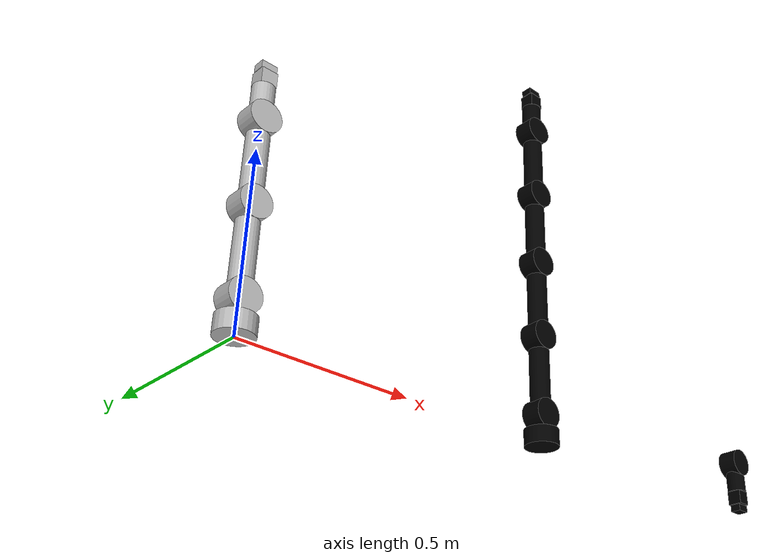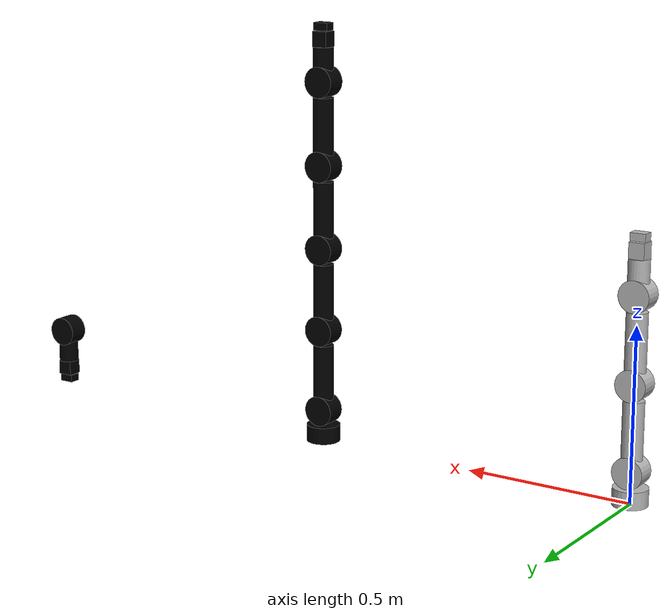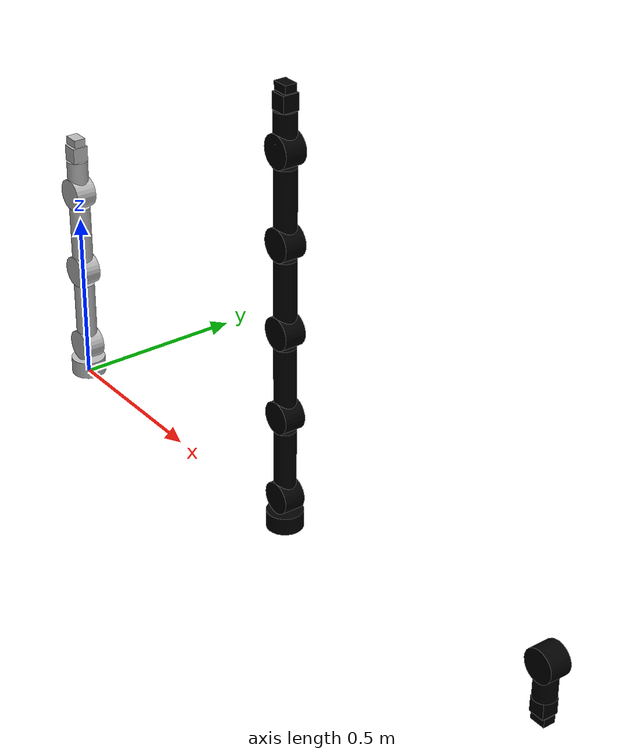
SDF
<?xml version='1.0'?>
<sdf version='1.6'>
  <model name='poke_modif'>
    <link name='poke_base_link'>
      <pose frame=''>0 0 0 0 -0 0</pose>
      <inertial>
        <pose frame=''>0 0 0.025 0 -0 0</pose>
        <mass>0.01</mass>
        <inertia>
          <ixx>0.0001</ixx>
          <ixy>0</ixy>
          <ixz>0</ixz>
          <iyy>0.0001</iyy>
          <iyz>0</iyz>
          <izz>0.0001</izz>
        </inertia>
      </inertial>
      <self_collide>0</self_collide>
      <enable_wind>0</enable_wind>
      <kinematic>0</kinematic>
      <visual name='poke_base_link_fixed_joint_lump__baseMount_link_visual'>
        <pose frame=''>0 0 0.025 0 -0 0</pose>
        <geometry>
          <cylinder>
            <length>0.05</length>
            <radius>0.05</radius>
          </cylinder>
        </geometry>
        <transparency>0</transparency>
        <cast_shadows>1</cast_shadows>
      </visual>
      <collision name='poke_base_link_fixed_joint_lump__baseMount_link_collision'>
        <laser_retro>0</laser_retro>
        <max_contacts>10</max_contacts>
        <pose frame=''>0 0 0.025 0 -0 0</pose>
        <geometry>
          <cylinder>
            <radius>0.05</radius>
            <length>0.05</length>
          </cylinder>
        </geometry>
        <surface>
          <friction>
            <ode>
              <mu>1</mu>
              <mu2>1</mu2>
              <fdir1>0 0 0</fdir1>
              <slip1>0</slip1>
              <slip2>0</slip2>
            </ode>
            <torsional>
              <coefficient>1</coefficient>
              <patch_radius>0</patch_radius>
              <surface_radius>0</surface_radius>
              <use_patch_radius>1</use_patch_radius>
              <ode>
                <slip>0</slip>
              </ode>
            </torsional>
          </friction>
          <bounce>
            <restitution_coefficient>0</restitution_coefficient>
            <threshold>1e+06</threshold>
          </bounce>
          <contact>
            <collide_without_contact>0</collide_without_contact>
            <collide_without_contact_bitmask>1</collide_without_contact_bitmask>
            <collide_bitmask>1</collide_bitmask>
            <ode>
              <soft_cfm>0</soft_cfm>
              <soft_erp>0.2</soft_erp>
              <kp>1e+13</kp>
              <kd>1</kd>
              <max_vel>0.01</max_vel>
              <min_depth>0</min_depth>
            </ode>
            <bullet>
              <split_impulse>1</split_impulse>
              <split_impulse_penetration_threshold>-0.01</split_impulse_penetration_threshold>
              <soft_cfm>0</soft_cfm>
              <soft_erp>0.2</soft_erp>
              <kp>1e+13</kp>
              <kd>1</kd>
            </bullet>
          </contact>
        </surface>
      </collision>
    </link>
    <link name='p0_link'>
      <pose frame=''>-0 0 0.095 0 -0 0</pose>
      <inertial>
        <pose frame=''>0 0 0.1 0 -0 0</pose>
        <mass>0.01</mass>
        <inertia>
          <ixx>0.0001</ixx>
          <ixy>0</ixy>
          <ixz>0</ixz>
          <iyy>0.0001</iyy>
          <iyz>0</iyz>
          <izz>0.0001</izz>
        </inertia>
      </inertial>
      <self_collide>0</self_collide>
      <enable_wind>0</enable_wind>
      <kinematic>0</kinematic>
      <visual name='p0_link_fixed_joint_lump__p0_joint_v_visual'>
        <pose frame=''>0 0 0 1.57079 -0 0</pose>
        <geometry>
          <cylinder>
            <length>0.06</length>
            <radius>0.045</radius>
          </cylinder>
        </geometry>
        <transparency>0</transparency>
        <cast_shadows>1</cast_shadows>
      </visual>
      <visual name='p0_link_fixed_joint_lump__p0_segmentL_v_visual_1'>
        <pose frame=''>0 0 0.1 0 -0 0</pose>
        <geometry>
          <cylinder>
            <length>0.2</length>
            <radius>0.03</radius>
          </cylinder>
        </geometry>
        <transparency>0</transparency>
        <cast_shadows>1</cast_shadows>
      </visual>
      <collision name='p0_link_fixed_joint_lump__p0_joint_c_collision'>
        <laser_retro>0</laser_retro>
        <max_contacts>10</max_contacts>
        <pose frame=''>0 0 0 1.57079 -0 0</pose>
        <geometry>
          <cylinder>
            <radius>0.045</radius>
            <length>0.06</length>
          </cylinder>
        </geometry>
        <surface>
          <friction>
            <ode>
              <mu>1</mu>
              <mu2>1</mu2>
              <fdir1>0 0 0</fdir1>
              <slip1>0</slip1>
              <slip2>0</slip2>
            </ode>
            <torsional>
              <coefficient>1</coefficient>
              <patch_radius>0</patch_radius>
              <surface_radius>0</surface_radius>
              <use_patch_radius>1</use_patch_radius>
              <ode>
                <slip>0</slip>
              </ode>
            </torsional>
          </friction>
          <bounce>
            <restitution_coefficient>0</restitution_coefficient>
            <threshold>1e+06</threshold>
          </bounce>
          <contact>
            <collide_without_contact>0</collide_without_contact>
            <collide_without_contact_bitmask>1</collide_without_contact_bitmask>
            <collide_bitmask>1</collide_bitmask>
            <ode>
              <soft_cfm>0</soft_cfm>
              <soft_erp>0.2</soft_erp>
              <kp>1e+13</kp>
              <kd>1</kd>
              <max_vel>0.01</max_vel>
              <min_depth>0</min_depth>
            </ode>
            <bullet>
              <split_impulse>1</split_impulse>
              <split_impulse_penetration_threshold>-0.01</split_impulse_penetration_threshold>
              <soft_cfm>0</soft_cfm>
              <soft_erp>0.2</soft_erp>
              <kp>1e+13</kp>
              <kd>1</kd>
            </bullet>
          </contact>
        </surface>
      </collision>
      <collision name='p0_link_fixed_joint_lump__p0_segmentL_c_collision_1'>
        <laser_retro>0</laser_retro>
        <max_contacts>10</max_contacts>
        <pose frame=''>0 0 0.1 0 -0 0</pose>
        <geometry>
          <cylinder>
            <radius>0.03</radius>
            <length>0.2</length>
          </cylinder>
        </geometry>
        <surface>
          <friction>
            <ode>
              <mu>1</mu>
              <mu2>1</mu2>
              <fdir1>0 0 0</fdir1>
              <slip1>0</slip1>
              <slip2>0</slip2>
            </ode>
            <torsional>
              <coefficient>1</coefficient>
              <patch_radius>0</patch_radius>
              <surface_radius>0</surface_radius>
              <use_patch_radius>1</use_patch_radius>
              <ode>
                <slip>0</slip>
              </ode>
            </torsional>
          </friction>
          <bounce>
            <restitution_coefficient>0</restitution_coefficient>
            <threshold>1e+06</threshold>
          </bounce>
          <contact>
            <collide_without_contact>0</collide_without_contact>
            <collide_without_contact_bitmask>1</collide_without_contact_bitmask>
            <collide_bitmask>1</collide_bitmask>
            <ode>
              <soft_cfm>0</soft_cfm>
              <soft_erp>0.2</soft_erp>
              <kp>1e+13</kp>
              <kd>1</kd>
              <max_vel>0.01</max_vel>
              <min_depth>0</min_depth>
            </ode>
            <bullet>
              <split_impulse>1</split_impulse>
              <split_impulse_penetration_threshold>-0.01</split_impulse_penetration_threshold>
              <soft_cfm>0</soft_cfm>
              <soft_erp>0.2</soft_erp>
              <kp>1e+13</kp>
              <kd>1</kd>
            </bullet>
          </contact>
        </surface>
      </collision>
    </link>
    <link name='p0_link_clone'>
      <pose frame=''>1 0 0.095 0 -0 0</pose>
      <inertial>
        <pose frame=''>0 0 0.1 0 -0 0</pose>
        <mass>0.01</mass>
        <inertia>
          <ixx>0.0001</ixx>
          <ixy>0</ixy>
          <ixz>0</ixz>
          <iyy>0.0001</iyy>
          <iyz>0</iyz>
          <izz>0.0001</izz>
        </inertia>
      </inertial>
      <self_collide>0</self_collide>
      <enable_wind>0</enable_wind>
      <kinematic>0</kinematic>
      <gravity>1</gravity>
      <visual name='p0_link_fixed_joint_lump__p0_joint_v_visual'>
        <pose frame=''>0 0 0 1.57079 -0 0</pose>
        <geometry>
          <cylinder>
            <length>0.06</length>
            <radius>0.045</radius>
          </cylinder>
        </geometry>
        <transparency>0</transparency>
        <cast_shadows>1</cast_shadows>
        <material>
          <shader type='vertex'>
            <normal_map>__default__</normal_map>
          </shader>
          <script>
            <name>ModelPreview_1::p0_link_clone::p0_link_fixed_joint_lump__p0_joint_v_visual_MATERIAL_</name>
          </script>
          <ambient>0 0 0 1</ambient>
          <diffuse>0 0 0 1</diffuse>
          <specular>0 0 0 1</specular>
          <emissive>0 0 0 1</emissive>
        </material>
      </visual>
      <visual name='p0_link_fixed_joint_lump__p0_segmentL_v_visual_1'>
        <pose frame=''>0 0 0.1 0 -0 0</pose>
        <geometry>
          <cylinder>
            <length>0.2</length>
            <radius>0.03</radius>
          </cylinder>
        </geometry>
        <transparency>0</transparency>
        <cast_shadows>1</cast_shadows>
        <material>
          <shader type='vertex'>
            <normal_map>__default__</normal_map>
          </shader>
          <script>
            <name>ModelPreview_1::p0_link_clone::p0_link_fixed_joint_lump__p0_segmentL_v_visual_1_MATERIAL_</name>
          </script>
          <ambient>0 0 0 1</ambient>
          <diffuse>0 0 0 1</diffuse>
          <specular>0 0 0 1</specular>
          <emissive>0 0 0 1</emissive>
        </material>
      </visual>
      <collision name='p0_link_fixed_joint_lump__p0_joint_c_collision'>
        <laser_retro>0</laser_retro>
        <max_contacts>10</max_contacts>
        <pose frame=''>0 0 0 1.57079 -0 0</pose>
        <geometry>
          <cylinder>
            <radius>0.045</radius>
            <length>0.06</length>
          </cylinder>
        </geometry>
        <surface>
          <friction>
            <ode>
              <mu>1</mu>
              <mu2>1</mu2>
              <fdir1>0 0 0</fdir1>
              <slip1>0</slip1>
              <slip2>0</slip2>
            </ode>
            <torsional>
              <coefficient>1</coefficient>
              <patch_radius>0</patch_radius>
              <surface_radius>0</surface_radius>
              <use_patch_radius>1</use_patch_radius>
              <ode>
                <slip>0</slip>
              </ode>
            </torsional>
          </friction>
          <bounce>
            <restitution_coefficient>0</restitution_coefficient>
            <threshold>1e+06</threshold>
          </bounce>
          <contact>
            <collide_without_contact>0</collide_without_contact>
            <collide_without_contact_bitmask>1</collide_without_contact_bitmask>
            <collide_bitmask>1</collide_bitmask>
            <ode>
              <soft_cfm>0</soft_cfm>
              <soft_erp>0.2</soft_erp>
              <kp>1e+13</kp>
              <kd>1</kd>
              <max_vel>0.01</max_vel>
              <min_depth>0</min_depth>
            </ode>
            <bullet>
              <split_impulse>1</split_impulse>
              <split_impulse_penetration_threshold>-0.01</split_impulse_penetration_threshold>
              <soft_cfm>0</soft_cfm>
              <soft_erp>0.2</soft_erp>
              <kp>1e+13</kp>
              <kd>1</kd>
            </bullet>
          </contact>
        </surface>
      </collision>
      <collision name='p0_link_fixed_joint_lump__p0_segmentL_c_collision_1'>
        <laser_retro>0</laser_retro>
        <max_contacts>10</max_contacts>
        <pose frame=''>0 0 0.1 0 -0 0</pose>
        <geometry>
          <cylinder>
            <radius>0.03</radius>
            <length>0.2</length>
          </cylinder>
        </geometry>
        <surface>
          <friction>
            <ode>
              <mu>1</mu>
              <mu2>1</mu2>
              <fdir1>0 0 0</fdir1>
              <slip1>0</slip1>
              <slip2>0</slip2>
            </ode>
            <torsional>
              <coefficient>1</coefficient>
              <patch_radius>0</patch_radius>
              <surface_radius>0</surface_radius>
              <use_patch_radius>1</use_patch_radius>
              <ode>
                <slip>0</slip>
              </ode>
            </torsional>
          </friction>
          <bounce>
            <restitution_coefficient>0</restitution_coefficient>
            <threshold>1e+06</threshold>
          </bounce>
          <contact>
            <collide_without_contact>0</collide_without_contact>
            <collide_without_contact_bitmask>1</collide_without_contact_bitmask>
            <collide_bitmask>1</collide_bitmask>
            <ode>
              <soft_cfm>0</soft_cfm>
              <soft_erp>0.2</soft_erp>
              <kp>1e+13</kp>
              <kd>1</kd>
              <max_vel>0.01</max_vel>
              <min_depth>0</min_depth>
            </ode>
            <bullet>
              <split_impulse>1</split_impulse>
              <split_impulse_penetration_threshold>-0.01</split_impulse_penetration_threshold>
              <soft_cfm>0</soft_cfm>
              <soft_erp>0.2</soft_erp>
              <kp>1e+13</kp>
              <kd>1</kd>
            </bullet>
          </contact>
        </surface>
      </collision>
    </link>
    <link name='p1_link'>
      <pose frame=''>-0 0 0.34 0 -0 0</pose>
      <inertial>
        <pose frame=''>0 0 0.1 0 -0 0</pose>
        <mass>0.01</mass>
        <inertia>
          <ixx>0.0001</ixx>
          <ixy>0</ixy>
          <ixz>0</ixz>
          <iyy>0.0001</iyy>
          <iyz>0</iyz>
          <izz>0.0001</izz>
        </inertia>
      </inertial>
      <self_collide>0</self_collide>
      <enable_wind>0</enable_wind>
      <kinematic>0</kinematic>
      <visual name='p1_link_fixed_joint_lump__p1_joint_v_visual'>
        <pose frame=''>0 0 0 1.57079 -0 0</pose>
        <geometry>
          <cylinder>
            <length>0.06</length>
            <radius>0.045</radius>
          </cylinder>
        </geometry>
        <transparency>0</transparency>
        <cast_shadows>1</cast_shadows>
      </visual>
      <visual name='p1_link_fixed_joint_lump__p1_segmentL_v_visual_1'>
        <pose frame=''>0 0 0.1 0 -0 0</pose>
        <geometry>
          <cylinder>
            <length>0.2</length>
            <radius>0.03</radius>
          </cylinder>
        </geometry>
        <transparency>0</transparency>
        <cast_shadows>1</cast_shadows>
      </visual>
      <collision name='p1_link_fixed_joint_lump__p1_joint_c_collision'>
        <laser_retro>0</laser_retro>
        <max_contacts>10</max_contacts>
        <pose frame=''>0 0 0 1.57079 -0 0</pose>
        <geometry>
          <cylinder>
            <radius>0.045</radius>
            <length>0.06</length>
          </cylinder>
        </geometry>
        <surface>
          <friction>
            <ode>
              <mu>1</mu>
              <mu2>1</mu2>
              <fdir1>0 0 0</fdir1>
              <slip1>0</slip1>
              <slip2>0</slip2>
            </ode>
            <torsional>
              <coefficient>1</coefficient>
              <patch_radius>0</patch_radius>
              <surface_radius>0</surface_radius>
              <use_patch_radius>1</use_patch_radius>
              <ode>
                <slip>0</slip>
              </ode>
            </torsional>
          </friction>
          <bounce>
            <restitution_coefficient>0</restitution_coefficient>
            <threshold>1e+06</threshold>
          </bounce>
          <contact>
            <collide_without_contact>0</collide_without_contact>
            <collide_without_contact_bitmask>1</collide_without_contact_bitmask>
            <collide_bitmask>1</collide_bitmask>
            <ode>
              <soft_cfm>0</soft_cfm>
              <soft_erp>0.2</soft_erp>
              <kp>1e+13</kp>
              <kd>1</kd>
              <max_vel>0.01</max_vel>
              <min_depth>0</min_depth>
            </ode>
            <bullet>
              <split_impulse>1</split_impulse>
              <split_impulse_penetration_threshold>-0.01</split_impulse_penetration_threshold>
              <soft_cfm>0</soft_cfm>
              <soft_erp>0.2</soft_erp>
              <kp>1e+13</kp>
              <kd>1</kd>
            </bullet>
          </contact>
        </surface>
      </collision>
      <collision name='p1_link_fixed_joint_lump__p1_segmentL_c_collision_1'>
        <laser_retro>0</laser_retro>
        <max_contacts>10</max_contacts>
        <pose frame=''>0 0 0.1 0 -0 0</pose>
        <geometry>
          <cylinder>
            <radius>0.03</radius>
            <length>0.2</length>
          </cylinder>
        </geometry>
        <surface>
          <friction>
            <ode>
              <mu>1</mu>
              <mu2>1</mu2>
              <fdir1>0 0 0</fdir1>
              <slip1>0</slip1>
              <slip2>0</slip2>
            </ode>
            <torsional>
              <coefficient>1</coefficient>
              <patch_radius>0</patch_radius>
              <surface_radius>0</surface_radius>
              <use_patch_radius>1</use_patch_radius>
              <ode>
                <slip>0</slip>
              </ode>
            </torsional>
          </friction>
          <bounce>
            <restitution_coefficient>0</restitution_coefficient>
            <threshold>1e+06</threshold>
          </bounce>
          <contact>
            <collide_without_contact>0</collide_without_contact>
            <collide_without_contact_bitmask>1</collide_without_contact_bitmask>
            <collide_bitmask>1</collide_bitmask>
            <ode>
              <soft_cfm>0</soft_cfm>
              <soft_erp>0.2</soft_erp>
              <kp>1e+13</kp>
              <kd>1</kd>
              <max_vel>0.01</max_vel>
              <min_depth>0</min_depth>
            </ode>
            <bullet>
              <split_impulse>1</split_impulse>
              <split_impulse_penetration_threshold>-0.01</split_impulse_penetration_threshold>
              <soft_cfm>0</soft_cfm>
              <soft_erp>0.2</soft_erp>
              <kp>1e+13</kp>
              <kd>1</kd>
            </bullet>
          </contact>
        </surface>
      </collision>
    </link>
    <link name='p1_link_clone'>
      <pose frame=''>1 -0 0.34 0 -0 0</pose>
      <inertial>
        <pose frame=''>0 0 0.1 0 -0 0</pose>
        <mass>0.01</mass>
        <inertia>
          <ixx>0.0001</ixx>
          <ixy>0</ixy>
          <ixz>0</ixz>
          <iyy>0.0001</iyy>
          <iyz>0</iyz>
          <izz>0.0001</izz>
        </inertia>
      </inertial>
      <self_collide>0</self_collide>
      <enable_wind>0</enable_wind>
      <kinematic>0</kinematic>
      <gravity>1</gravity>
      <visual name='p1_link_fixed_joint_lump__p1_joint_v_visual'>
        <pose frame=''>0 0 0 1.57079 -0 0</pose>
        <geometry>
          <cylinder>
            <length>0.06</length>
            <radius>0.045</radius>
          </cylinder>
        </geometry>
        <transparency>0</transparency>
        <cast_shadows>1</cast_shadows>
        <material>
          <shader type='vertex'>
            <normal_map>__default__</normal_map>
          </shader>
          <script>
            <name>ModelPreview_1::p1_link_clone::p1_link_fixed_joint_lump__p1_joint_v_visual_MATERIAL_</name>
          </script>
          <ambient>0 0 0 1</ambient>
          <diffuse>0 0 0 1</diffuse>
          <specular>0 0 0 1</specular>
          <emissive>0 0 0 1</emissive>
        </material>
      </visual>
      <visual name='p1_link_fixed_joint_lump__p1_segmentL_v_visual_1'>
        <pose frame=''>0 0 0.1 0 -0 0</pose>
        <geometry>
          <cylinder>
            <length>0.2</length>
            <radius>0.03</radius>
          </cylinder>
        </geometry>
        <transparency>0</transparency>
        <cast_shadows>1</cast_shadows>
        <material>
          <shader type='vertex'>
            <normal_map>__default__</normal_map>
          </shader>
          <script>
            <name>ModelPreview_1::p1_link_clone::p1_link_fixed_joint_lump__p1_segmentL_v_visual_1_MATERIAL_</name>
          </script>
          <ambient>0 0 0 1</ambient>
          <diffuse>0 0 0 1</diffuse>
          <specular>0 0 0 1</specular>
          <emissive>0 0 0 1</emissive>
        </material>
      </visual>
      <collision name='p1_link_fixed_joint_lump__p1_joint_c_collision'>
        <laser_retro>0</laser_retro>
        <max_contacts>10</max_contacts>
        <pose frame=''>0 0 0 1.57079 -0 0</pose>
        <geometry>
          <cylinder>
            <radius>0.045</radius>
            <length>0.06</length>
          </cylinder>
        </geometry>
        <surface>
          <friction>
            <ode>
              <mu>1</mu>
              <mu2>1</mu2>
              <fdir1>0 0 0</fdir1>
              <slip1>0</slip1>
              <slip2>0</slip2>
            </ode>
            <torsional>
              <coefficient>1</coefficient>
              <patch_radius>0</patch_radius>
              <surface_radius>0</surface_radius>
              <use_patch_radius>1</use_patch_radius>
              <ode>
                <slip>0</slip>
              </ode>
            </torsional>
          </friction>
          <bounce>
            <restitution_coefficient>0</restitution_coefficient>
            <threshold>1e+06</threshold>
          </bounce>
          <contact>
            <collide_without_contact>0</collide_without_contact>
            <collide_without_contact_bitmask>1</collide_without_contact_bitmask>
            <collide_bitmask>1</collide_bitmask>
            <ode>
              <soft_cfm>0</soft_cfm>
              <soft_erp>0.2</soft_erp>
              <kp>1e+13</kp>
              <kd>1</kd>
              <max_vel>0.01</max_vel>
              <min_depth>0</min_depth>
            </ode>
            <bullet>
              <split_impulse>1</split_impulse>
              <split_impulse_penetration_threshold>-0.01</split_impulse_penetration_threshold>
              <soft_cfm>0</soft_cfm>
              <soft_erp>0.2</soft_erp>
              <kp>1e+13</kp>
              <kd>1</kd>
            </bullet>
          </contact>
        </surface>
      </collision>
      <collision name='p1_link_fixed_joint_lump__p1_segmentL_c_collision_1'>
        <laser_retro>0</laser_retro>
        <max_contacts>10</max_contacts>
        <pose frame=''>0 0 0.1 0 -0 0</pose>
        <geometry>
          <cylinder>
            <radius>0.03</radius>
            <length>0.2</length>
          </cylinder>
        </geometry>
        <surface>
          <friction>
            <ode>
              <mu>1</mu>
              <mu2>1</mu2>
              <fdir1>0 0 0</fdir1>
              <slip1>0</slip1>
              <slip2>0</slip2>
            </ode>
            <torsional>
              <coefficient>1</coefficient>
              <patch_radius>0</patch_radius>
              <surface_radius>0</surface_radius>
              <use_patch_radius>1</use_patch_radius>
              <ode>
                <slip>0</slip>
              </ode>
            </torsional>
          </friction>
          <bounce>
            <restitution_coefficient>0</restitution_coefficient>
            <threshold>1e+06</threshold>
          </bounce>
          <contact>
            <collide_without_contact>0</collide_without_contact>
            <collide_without_contact_bitmask>1</collide_without_contact_bitmask>
            <collide_bitmask>1</collide_bitmask>
            <ode>
              <soft_cfm>0</soft_cfm>
              <soft_erp>0.2</soft_erp>
              <kp>1e+13</kp>
              <kd>1</kd>
              <max_vel>0.01</max_vel>
              <min_depth>0</min_depth>
            </ode>
            <bullet>
              <split_impulse>1</split_impulse>
              <split_impulse_penetration_threshold>-0.01</split_impulse_penetration_threshold>
              <soft_cfm>0</soft_cfm>
              <soft_erp>0.2</soft_erp>
              <kp>1e+13</kp>
              <kd>1</kd>
            </bullet>
          </contact>
        </surface>
      </collision>
    </link>
    <link name='p1_link_clone_clone'>
      <pose frame=''>1 -0 0.585 0 -0 0</pose>
      <inertial>
        <pose frame=''>0 0 0.1 0 -0 0</pose>
        <mass>0.01</mass>
        <inertia>
          <ixx>0.0001</ixx>
          <ixy>0</ixy>
          <ixz>0</ixz>
          <iyy>0.0001</iyy>
          <iyz>0</iyz>
          <izz>0.0001</izz>
        </inertia>
      </inertial>
      <self_collide>0</self_collide>
      <enable_wind>0</enable_wind>
      <kinematic>0</kinematic>
      <gravity>1</gravity>
      <visual name='p1_link_fixed_joint_lump__p1_joint_v_visual'>
        <pose frame=''>0 0 0 1.57079 -0 0</pose>
        <geometry>
          <cylinder>
            <length>0.06</length>
            <radius>0.045</radius>
          </cylinder>
        </geometry>
        <transparency>0</transparency>
        <cast_shadows>1</cast_shadows>
        <material>
          <shader type='vertex'>
            <normal_map>__default__</normal_map>
          </shader>
          <script>
            <name>ModelPreview_1::p1_link_clone::p1_link_fixed_joint_lump__p1_joint_v_visual_MATERIAL_</name>
            <uri>__default__</uri>
          </script>
          <ambient>0 0 0 1</ambient>
          <diffuse>0 0 0 1</diffuse>
          <specular>0 0 0 1</specular>
          <emissive>0 0 0 1</emissive>
        </material>
      </visual>
      <visual name='p1_link_fixed_joint_lump__p1_segmentL_v_visual_1'>
        <pose frame=''>0 0 0.1 0 -0 0</pose>
        <geometry>
          <cylinder>
            <length>0.2</length>
            <radius>0.03</radius>
          </cylinder>
        </geometry>
        <transparency>0</transparency>
        <cast_shadows>1</cast_shadows>
        <material>
          <shader type='vertex'>
            <normal_map>__default__</normal_map>
          </shader>
          <script>
            <name>ModelPreview_1::p1_link_clone::p1_link_fixed_joint_lump__p1_segmentL_v_visual_1_MATERIAL_</name>
            <uri>__default__</uri>
          </script>
          <ambient>0 0 0 1</ambient>
          <diffuse>0 0 0 1</diffuse>
          <specular>0 0 0 1</specular>
          <emissive>0 0 0 1</emissive>
        </material>
      </visual>
      <collision name='p1_link_fixed_joint_lump__p1_joint_c_collision'>
        <laser_retro>0</laser_retro>
        <max_contacts>10</max_contacts>
        <pose frame=''>0 0 0 1.57079 -0 0</pose>
        <geometry>
          <cylinder>
            <radius>0.045</radius>
            <length>0.06</length>
          </cylinder>
        </geometry>
        <surface>
          <friction>
            <ode>
              <mu>1</mu>
              <mu2>1</mu2>
              <fdir1>0 0 0</fdir1>
              <slip1>0</slip1>
              <slip2>0</slip2>
            </ode>
            <torsional>
              <coefficient>1</coefficient>
              <patch_radius>0</patch_radius>
              <surface_radius>0</surface_radius>
              <use_patch_radius>1</use_patch_radius>
              <ode>
                <slip>0</slip>
              </ode>
            </torsional>
          </friction>
          <bounce>
            <restitution_coefficient>0</restitution_coefficient>
            <threshold>1e+06</threshold>
          </bounce>
          <contact>
            <collide_without_contact>0</collide_without_contact>
            <collide_without_contact_bitmask>1</collide_without_contact_bitmask>
            <collide_bitmask>1</collide_bitmask>
            <ode>
              <soft_cfm>0</soft_cfm>
              <soft_erp>0.2</soft_erp>
              <kp>1e+13</kp>
              <kd>1</kd>
              <max_vel>0.01</max_vel>
              <min_depth>0</min_depth>
            </ode>
            <bullet>
              <split_impulse>1</split_impulse>
              <split_impulse_penetration_threshold>-0.01</split_impulse_penetration_threshold>
              <soft_cfm>0</soft_cfm>
              <soft_erp>0.2</soft_erp>
              <kp>1e+13</kp>
              <kd>1</kd>
            </bullet>
          </contact>
        </surface>
      </collision>
      <collision name='p1_link_fixed_joint_lump__p1_segmentL_c_collision_1'>
        <laser_retro>0</laser_retro>
        <max_contacts>10</max_contacts>
        <pose frame=''>0 0 0.1 0 -0 0</pose>
        <geometry>
          <cylinder>
            <radius>0.03</radius>
            <length>0.2</length>
          </cylinder>
        </geometry>
        <surface>
          <friction>
            <ode>
              <mu>1</mu>
              <mu2>1</mu2>
              <fdir1>0 0 0</fdir1>
              <slip1>0</slip1>
              <slip2>0</slip2>
            </ode>
            <torsional>
              <coefficient>1</coefficient>
              <patch_radius>0</patch_radius>
              <surface_radius>0</surface_radius>
              <use_patch_radius>1</use_patch_radius>
              <ode>
                <slip>0</slip>
              </ode>
            </torsional>
          </friction>
          <bounce>
            <restitution_coefficient>0</restitution_coefficient>
            <threshold>1e+06</threshold>
          </bounce>
          <contact>
            <collide_without_contact>0</collide_without_contact>
            <collide_without_contact_bitmask>1</collide_without_contact_bitmask>
            <collide_bitmask>1</collide_bitmask>
            <ode>
              <soft_cfm>0</soft_cfm>
              <soft_erp>0.2</soft_erp>
              <kp>1e+13</kp>
              <kd>1</kd>
              <max_vel>0.01</max_vel>
              <min_depth>0</min_depth>
            </ode>
            <bullet>
              <split_impulse>1</split_impulse>
              <split_impulse_penetration_threshold>-0.01</split_impulse_penetration_threshold>
              <soft_cfm>0</soft_cfm>
              <soft_erp>0.2</soft_erp>
              <kp>1e+13</kp>
              <kd>1</kd>
            </bullet>
          </contact>
        </surface>
      </collision>
    </link>
    <link name='p1_link_clone_clone_clone'>
      <pose frame=''>1 -0 0.83 0 -0 0</pose>
      <inertial>
        <pose frame=''>0 0 0.1 0 -0 0</pose>
        <mass>0.01</mass>
        <inertia>
          <ixx>0.0001</ixx>
          <ixy>0</ixy>
          <ixz>0</ixz>
          <iyy>0.0001</iyy>
          <iyz>0</iyz>
          <izz>0.0001</izz>
        </inertia>
      </inertial>
      <self_collide>0</self_collide>
      <enable_wind>0</enable_wind>
      <kinematic>0</kinematic>
      <gravity>1</gravity>
      <visual name='p1_link_fixed_joint_lump__p1_joint_v_visual'>
        <pose frame=''>0 0 0 1.57079 -0 0</pose>
        <geometry>
          <cylinder>
            <length>0.06</length>
            <radius>0.045</radius>
          </cylinder>
        </geometry>
        <transparency>0</transparency>
        <cast_shadows>1</cast_shadows>
        <material>
          <shader type='vertex'>
            <normal_map>__default__</normal_map>
          </shader>
          <script>
            <name>ModelPreview_1::p1_link_clone::p1_link_fixed_joint_lump__p1_joint_v_visual_MATERIAL_</name>
            <uri>__default__</uri>
          </script>
          <ambient>0 0 0 1</ambient>
          <diffuse>0 0 0 1</diffuse>
          <specular>0 0 0 1</specular>
          <emissive>0 0 0 1</emissive>
        </material>
      </visual>
      <visual name='p1_link_fixed_joint_lump__p1_segmentL_v_visual_1'>
        <pose frame=''>0 0 0.1 0 -0 0</pose>
        <geometry>
          <cylinder>
            <length>0.2</length>
            <radius>0.03</radius>
          </cylinder>
        </geometry>
        <transparency>0</transparency>
        <cast_shadows>1</cast_shadows>
        <material>
          <shader type='vertex'>
            <normal_map>__default__</normal_map>
          </shader>
          <script>
            <name>ModelPreview_1::p1_link_clone::p1_link_fixed_joint_lump__p1_segmentL_v_visual_1_MATERIAL_</name>
            <uri>__default__</uri>
          </script>
          <ambient>0 0 0 1</ambient>
          <diffuse>0 0 0 1</diffuse>
          <specular>0 0 0 1</specular>
          <emissive>0 0 0 1</emissive>
        </material>
      </visual>
      <collision name='p1_link_fixed_joint_lump__p1_joint_c_collision'>
        <laser_retro>0</laser_retro>
        <max_contacts>10</max_contacts>
        <pose frame=''>0 0 0 1.57079 -0 0</pose>
        <geometry>
          <cylinder>
            <radius>0.045</radius>
            <length>0.06</length>
          </cylinder>
        </geometry>
        <surface>
          <friction>
            <ode>
              <mu>1</mu>
              <mu2>1</mu2>
              <fdir1>0 0 0</fdir1>
              <slip1>0</slip1>
              <slip2>0</slip2>
            </ode>
            <torsional>
              <coefficient>1</coefficient>
              <patch_radius>0</patch_radius>
              <surface_radius>0</surface_radius>
              <use_patch_radius>1</use_patch_radius>
              <ode>
                <slip>0</slip>
              </ode>
            </torsional>
          </friction>
          <bounce>
            <restitution_coefficient>0</restitution_coefficient>
            <threshold>1e+06</threshold>
          </bounce>
          <contact>
            <collide_without_contact>0</collide_without_contact>
            <collide_without_contact_bitmask>1</collide_without_contact_bitmask>
            <collide_bitmask>1</collide_bitmask>
            <ode>
              <soft_cfm>0</soft_cfm>
              <soft_erp>0.2</soft_erp>
              <kp>1e+13</kp>
              <kd>1</kd>
              <max_vel>0.01</max_vel>
              <min_depth>0</min_depth>
            </ode>
            <bullet>
              <split_impulse>1</split_impulse>
              <split_impulse_penetration_threshold>-0.01</split_impulse_penetration_threshold>
              <soft_cfm>0</soft_cfm>
              <soft_erp>0.2</soft_erp>
              <kp>1e+13</kp>
              <kd>1</kd>
            </bullet>
          </contact>
        </surface>
      </collision>
      <collision name='p1_link_fixed_joint_lump__p1_segmentL_c_collision_1'>
        <laser_retro>0</laser_retro>
        <max_contacts>10</max_contacts>
        <pose frame=''>0 0 0.1 0 -0 0</pose>
        <geometry>
          <cylinder>
            <radius>0.03</radius>
            <length>0.2</length>
          </cylinder>
        </geometry>
        <surface>
          <friction>
            <ode>
              <mu>1</mu>
              <mu2>1</mu2>
              <fdir1>0 0 0</fdir1>
              <slip1>0</slip1>
              <slip2>0</slip2>
            </ode>
            <torsional>
              <coefficient>1</coefficient>
              <patch_radius>0</patch_radius>
              <surface_radius>0</surface_radius>
              <use_patch_radius>1</use_patch_radius>
              <ode>
                <slip>0</slip>
              </ode>
            </torsional>
          </friction>
          <bounce>
            <restitution_coefficient>0</restitution_coefficient>
            <threshold>1e+06</threshold>
          </bounce>
          <contact>
            <collide_without_contact>0</collide_without_contact>
            <collide_without_contact_bitmask>1</collide_without_contact_bitmask>
            <collide_bitmask>1</collide_bitmask>
            <ode>
              <soft_cfm>0</soft_cfm>
              <soft_erp>0.2</soft_erp>
              <kp>1e+13</kp>
              <kd>1</kd>
              <max_vel>0.01</max_vel>
              <min_depth>0</min_depth>
            </ode>
            <bullet>
              <split_impulse>1</split_impulse>
              <split_impulse_penetration_threshold>-0.01</split_impulse_penetration_threshold>
              <soft_cfm>0</soft_cfm>
              <soft_erp>0.2</soft_erp>
              <kp>1e+13</kp>
              <kd>1</kd>
            </bullet>
          </contact>
        </surface>
      </collision>
    </link>
    <link name='p2_link'>
      <pose frame=''>0 -0 0.585 0 -0 0</pose>
      <inertial>
        <pose frame=''>0 0 0.05 0 -0 0</pose>
        <mass>0.01</mass>
        <inertia>
          <ixx>0.0001</ixx>
          <ixy>0</ixy>
          <ixz>0</ixz>
          <iyy>0.0001</iyy>
          <iyz>0</iyz>
          <izz>0.0001</izz>
        </inertia>
      </inertial>
      <self_collide>0</self_collide>
      <enable_wind>0</enable_wind>
      <kinematic>0</kinematic>
      <visual name='p2_link_fixed_joint_lump__p2_joint_v_visual'>
        <pose frame=''>0 0 0 1.57079 -0 0</pose>
        <geometry>
          <cylinder>
            <length>0.06</length>
            <radius>0.045</radius>
          </cylinder>
        </geometry>
        <transparency>0</transparency>
        <cast_shadows>1</cast_shadows>
      </visual>
      <visual name='p2_link_fixed_joint_lump__p2_segmentS_v_visual_1'>
        <pose frame=''>0 0 0.05 0 -0 0</pose>
        <geometry>
          <cylinder>
            <length>0.1</length>
            <radius>0.03</radius>
          </cylinder>
        </geometry>
        <transparency>0</transparency>
        <cast_shadows>1</cast_shadows>
      </visual>
      <collision name='p2_link_fixed_joint_lump__p2_joint_c_collision'>
        <laser_retro>0</laser_retro>
        <max_contacts>10</max_contacts>
        <pose frame=''>0 0 0 1.57079 -0 0</pose>
        <geometry>
          <cylinder>
            <radius>0.045</radius>
            <length>0.06</length>
          </cylinder>
        </geometry>
        <surface>
          <friction>
            <ode>
              <mu>1</mu>
              <mu2>1</mu2>
              <fdir1>0 0 0</fdir1>
              <slip1>0</slip1>
              <slip2>0</slip2>
            </ode>
            <torsional>
              <coefficient>1</coefficient>
              <patch_radius>0</patch_radius>
              <surface_radius>0</surface_radius>
              <use_patch_radius>1</use_patch_radius>
              <ode>
                <slip>0</slip>
              </ode>
            </torsional>
          </friction>
          <bounce>
            <restitution_coefficient>0</restitution_coefficient>
            <threshold>1e+06</threshold>
          </bounce>
          <contact>
            <collide_without_contact>0</collide_without_contact>
            <collide_without_contact_bitmask>1</collide_without_contact_bitmask>
            <collide_bitmask>1</collide_bitmask>
            <ode>
              <soft_cfm>0</soft_cfm>
              <soft_erp>0.2</soft_erp>
              <kp>1e+13</kp>
              <kd>1</kd>
              <max_vel>0.01</max_vel>
              <min_depth>0</min_depth>
            </ode>
            <bullet>
              <split_impulse>1</split_impulse>
              <split_impulse_penetration_threshold>-0.01</split_impulse_penetration_threshold>
              <soft_cfm>0</soft_cfm>
              <soft_erp>0.2</soft_erp>
              <kp>1e+13</kp>
              <kd>1</kd>
            </bullet>
          </contact>
        </surface>
      </collision>
      <collision name='p2_link_fixed_joint_lump__p2_segmentS_c_collision_1'>
        <laser_retro>0</laser_retro>
        <max_contacts>10</max_contacts>
        <pose frame=''>0 0 0.05 0 -0 0</pose>
        <geometry>
          <cylinder>
            <radius>0.03</radius>
            <length>0.1</length>
          </cylinder>
        </geometry>
        <surface>
          <friction>
            <ode>
              <mu>1</mu>
              <mu2>1</mu2>
              <fdir1>0 0 0</fdir1>
              <slip1>0</slip1>
              <slip2>0</slip2>
            </ode>
            <torsional>
              <coefficient>1</coefficient>
              <patch_radius>0</patch_radius>
              <surface_radius>0</surface_radius>
              <use_patch_radius>1</use_patch_radius>
              <ode>
                <slip>0</slip>
              </ode>
            </torsional>
          </friction>
          <bounce>
            <restitution_coefficient>0</restitution_coefficient>
            <threshold>1e+06</threshold>
          </bounce>
          <contact>
            <collide_without_contact>0</collide_without_contact>
            <collide_without_contact_bitmask>1</collide_without_contact_bitmask>
            <collide_bitmask>1</collide_bitmask>
            <ode>
              <soft_cfm>0</soft_cfm>
              <soft_erp>0.2</soft_erp>
              <kp>1e+13</kp>
              <kd>1</kd>
              <max_vel>0.01</max_vel>
              <min_depth>0</min_depth>
            </ode>
            <bullet>
              <split_impulse>1</split_impulse>
              <split_impulse_penetration_threshold>-0.01</split_impulse_penetration_threshold>
              <soft_cfm>0</soft_cfm>
              <soft_erp>0.2</soft_erp>
              <kp>1e+13</kp>
              <kd>1</kd>
            </bullet>
          </contact>
        </surface>
      </collision>
    </link>
    <link name='p2_link_clone'>
      <pose frame=''>1 -0 1.075 0 -0 0</pose>
      <inertial>
        <pose frame=''>0 0 0.05 0 -0 0</pose>
        <mass>0.01</mass>
        <inertia>
          <ixx>0.0001</ixx>
          <ixy>0</ixy>
          <ixz>0</ixz>
          <iyy>0.0001</iyy>
          <iyz>0</iyz>
          <izz>0.0001</izz>
        </inertia>
      </inertial>
      <self_collide>0</self_collide>
      <enable_wind>0</enable_wind>
      <kinematic>0</kinematic>
      <gravity>1</gravity>
      <visual name='p2_link_fixed_joint_lump__p2_joint_v_visual'>
        <pose frame=''>0 0 0 1.57079 -0 0</pose>
        <geometry>
          <cylinder>
            <length>0.06</length>
            <radius>0.045</radius>
          </cylinder>
        </geometry>
        <transparency>0</transparency>
        <cast_shadows>1</cast_shadows>
        <material>
          <shader type='vertex'>
            <normal_map>__default__</normal_map>
          </shader>
          <script>
            <name>ModelPreview_1::p2_link_clone::p2_link_fixed_joint_lump__p2_joint_v_visual_MATERIAL_</name>
          </script>
          <ambient>0 0 0 1</ambient>
          <diffuse>0 0 0 1</diffuse>
          <specular>0 0 0 1</specular>
          <emissive>0 0 0 1</emissive>
        </material>
      </visual>
      <visual name='p2_link_fixed_joint_lump__p2_segmentS_v_visual_1'>
        <pose frame=''>0 0 0.05 0 -0 0</pose>
        <geometry>
          <cylinder>
            <length>0.1</length>
            <radius>0.03</radius>
          </cylinder>
        </geometry>
        <transparency>0</transparency>
        <cast_shadows>1</cast_shadows>
        <material>
          <shader type='vertex'>
            <normal_map>__default__</normal_map>
          </shader>
          <script>
            <name>ModelPreview_1::p2_link_clone::p2_link_fixed_joint_lump__p2_segmentS_v_visual_1_MATERIAL_</name>
          </script>
          <ambient>0 0 0 1</ambient>
          <diffuse>0 0 0 1</diffuse>
          <specular>0 0 0 1</specular>
          <emissive>0 0 0 1</emissive>
        </material>
      </visual>
      <collision name='p2_link_fixed_joint_lump__p2_joint_c_collision'>
        <laser_retro>0</laser_retro>
        <max_contacts>10</max_contacts>
        <pose frame=''>0 0 0 1.57079 -0 0</pose>
        <geometry>
          <cylinder>
            <radius>0.045</radius>
            <length>0.06</length>
          </cylinder>
        </geometry>
        <surface>
          <friction>
            <ode>
              <mu>1</mu>
              <mu2>1</mu2>
              <fdir1>0 0 0</fdir1>
              <slip1>0</slip1>
              <slip2>0</slip2>
            </ode>
            <torsional>
              <coefficient>1</coefficient>
              <patch_radius>0</patch_radius>
              <surface_radius>0</surface_radius>
              <use_patch_radius>1</use_patch_radius>
              <ode>
                <slip>0</slip>
              </ode>
            </torsional>
          </friction>
          <bounce>
            <restitution_coefficient>0</restitution_coefficient>
            <threshold>1e+06</threshold>
          </bounce>
          <contact>
            <collide_without_contact>0</collide_without_contact>
            <collide_without_contact_bitmask>1</collide_without_contact_bitmask>
            <collide_bitmask>1</collide_bitmask>
            <ode>
              <soft_cfm>0</soft_cfm>
              <soft_erp>0.2</soft_erp>
              <kp>1e+13</kp>
              <kd>1</kd>
              <max_vel>0.01</max_vel>
              <min_depth>0</min_depth>
            </ode>
            <bullet>
              <split_impulse>1</split_impulse>
              <split_impulse_penetration_threshold>-0.01</split_impulse_penetration_threshold>
              <soft_cfm>0</soft_cfm>
              <soft_erp>0.2</soft_erp>
              <kp>1e+13</kp>
              <kd>1</kd>
            </bullet>
          </contact>
        </surface>
      </collision>
      <collision name='p2_link_fixed_joint_lump__p2_segmentS_c_collision_1'>
        <laser_retro>0</laser_retro>
        <max_contacts>10</max_contacts>
        <pose frame=''>0 0 0.05 0 -0 0</pose>
        <geometry>
          <cylinder>
            <radius>0.03</radius>
            <length>0.1</length>
          </cylinder>
        </geometry>
        <surface>
          <friction>
            <ode>
              <mu>1</mu>
              <mu2>1</mu2>
              <fdir1>0 0 0</fdir1>
              <slip1>0</slip1>
              <slip2>0</slip2>
            </ode>
            <torsional>
              <coefficient>1</coefficient>
              <patch_radius>0</patch_radius>
              <surface_radius>0</surface_radius>
              <use_patch_radius>1</use_patch_radius>
              <ode>
                <slip>0</slip>
              </ode>
            </torsional>
          </friction>
          <bounce>
            <restitution_coefficient>0</restitution_coefficient>
            <threshold>1e+06</threshold>
          </bounce>
          <contact>
            <collide_without_contact>0</collide_without_contact>
            <collide_without_contact_bitmask>1</collide_without_contact_bitmask>
            <collide_bitmask>1</collide_bitmask>
            <ode>
              <soft_cfm>0</soft_cfm>
              <soft_erp>0.2</soft_erp>
              <kp>1e+13</kp>
              <kd>1</kd>
              <max_vel>0.01</max_vel>
              <min_depth>0</min_depth>
            </ode>
            <bullet>
              <split_impulse>1</split_impulse>
              <split_impulse_penetration_threshold>-0.01</split_impulse_penetration_threshold>
              <soft_cfm>0</soft_cfm>
              <soft_erp>0.2</soft_erp>
              <kp>1e+13</kp>
              <kd>1</kd>
            </bullet>
          </contact>
        </surface>
      </collision>
    </link>
    <link name='p2_link_clone_0'>
      <pose frame=''>2 -0 0.19 3.14159 3e-06 3.14159</pose>
      <inertial>
        <pose frame=''>0 0 0.05 0 -0 0</pose>
        <mass>0.01</mass>
        <inertia>
          <ixx>0.0001</ixx>
          <ixy>0</ixy>
          <ixz>0</ixz>
          <iyy>0.0001</iyy>
          <iyz>0</iyz>
          <izz>0.0001</izz>
        </inertia>
      </inertial>
      <self_collide>0</self_collide>
      <enable_wind>0</enable_wind>
      <kinematic>0</kinematic>
      <gravity>1</gravity>
      <visual name='p2_link_fixed_joint_lump__p2_joint_v_visual'>
        <pose frame=''>0 0 0 1.57079 -0 0</pose>
        <geometry>
          <cylinder>
            <length>0.06</length>
            <radius>0.045</radius>
          </cylinder>
        </geometry>
        <transparency>0</transparency>
        <cast_shadows>1</cast_shadows>
        <material>
          <shader type='vertex'>
            <normal_map>__default__</normal_map>
          </shader>
          <script>
            <name>ModelPreview_1::p2_link_clone_0::p2_link_fixed_joint_lump__p2_joint_v_visual_MATERIAL_</name>
          </script>
          <ambient>0 0 0 1</ambient>
          <diffuse>0 0 0 1</diffuse>
          <specular>0 0 0 1</specular>
          <emissive>0 0 0 1</emissive>
        </material>
      </visual>
      <visual name='p2_link_fixed_joint_lump__p2_segmentS_v_visual_1'>
        <pose frame=''>0 0 0.05 0 -0 0</pose>
        <geometry>
          <cylinder>
            <length>0.1</length>
            <radius>0.03</radius>
          </cylinder>
        </geometry>
        <transparency>0</transparency>
        <cast_shadows>1</cast_shadows>
        <material>
          <shader type='vertex'>
            <normal_map>__default__</normal_map>
          </shader>
          <script>
            <name>ModelPreview_1::p2_link_clone_0::p2_link_fixed_joint_lump__p2_segmentS_v_visual_1_MATERIAL_</name>
          </script>
          <ambient>0 0 0 1</ambient>
          <diffuse>0 0 0 1</diffuse>
          <specular>0 0 0 1</specular>
          <emissive>0 0 0 1</emissive>
        </material>
      </visual>
      <collision name='p2_link_fixed_joint_lump__p2_joint_c_collision'>
        <laser_retro>0</laser_retro>
        <max_contacts>10</max_contacts>
        <pose frame=''>0 0 0 1.57079 -0 0</pose>
        <geometry>
          <cylinder>
            <radius>0.045</radius>
            <length>0.06</length>
          </cylinder>
        </geometry>
        <surface>
          <friction>
            <ode>
              <mu>1</mu>
              <mu2>1</mu2>
              <fdir1>0 0 0</fdir1>
              <slip1>0</slip1>
              <slip2>0</slip2>
            </ode>
            <torsional>
              <coefficient>1</coefficient>
              <patch_radius>0</patch_radius>
              <surface_radius>0</surface_radius>
              <use_patch_radius>1</use_patch_radius>
              <ode>
                <slip>0</slip>
              </ode>
            </torsional>
          </friction>
          <bounce>
            <restitution_coefficient>0</restitution_coefficient>
            <threshold>1e+06</threshold>
          </bounce>
          <contact>
            <collide_without_contact>0</collide_without_contact>
            <collide_without_contact_bitmask>1</collide_without_contact_bitmask>
            <collide_bitmask>1</collide_bitmask>
            <ode>
              <soft_cfm>0</soft_cfm>
              <soft_erp>0.2</soft_erp>
              <kp>1e+13</kp>
              <kd>1</kd>
              <max_vel>0.01</max_vel>
              <min_depth>0</min_depth>
            </ode>
            <bullet>
              <split_impulse>1</split_impulse>
              <split_impulse_penetration_threshold>-0.01</split_impulse_penetration_threshold>
              <soft_cfm>0</soft_cfm>
              <soft_erp>0.2</soft_erp>
              <kp>1e+13</kp>
              <kd>1</kd>
            </bullet>
          </contact>
        </surface>
      </collision>
      <collision name='p2_link_fixed_joint_lump__p2_segmentS_c_collision_1'>
        <laser_retro>0</laser_retro>
        <max_contacts>10</max_contacts>
        <pose frame=''>0 0 0.05 0 -0 0</pose>
        <geometry>
          <cylinder>
            <radius>0.03</radius>
            <length>0.1</length>
          </cylinder>
        </geometry>
        <surface>
          <friction>
            <ode>
              <mu>1</mu>
              <mu2>1</mu2>
              <fdir1>0 0 0</fdir1>
              <slip1>0</slip1>
              <slip2>0</slip2>
            </ode>
            <torsional>
              <coefficient>1</coefficient>
              <patch_radius>0</patch_radius>
              <surface_radius>0</surface_radius>
              <use_patch_radius>1</use_patch_radius>
              <ode>
                <slip>0</slip>
              </ode>
            </torsional>
          </friction>
          <bounce>
            <restitution_coefficient>0</restitution_coefficient>
            <threshold>1e+06</threshold>
          </bounce>
          <contact>
            <collide_without_contact>0</collide_without_contact>
            <collide_without_contact_bitmask>1</collide_without_contact_bitmask>
            <collide_bitmask>1</collide_bitmask>
            <ode>
              <soft_cfm>0</soft_cfm>
              <soft_erp>0.2</soft_erp>
              <kp>1e+13</kp>
              <kd>1</kd>
              <max_vel>0.01</max_vel>
              <min_depth>0</min_depth>
            </ode>
            <bullet>
              <split_impulse>1</split_impulse>
              <split_impulse_penetration_threshold>-0.01</split_impulse_penetration_threshold>
              <soft_cfm>0</soft_cfm>
              <soft_erp>0.2</soft_erp>
              <kp>1e+13</kp>
              <kd>1</kd>
            </bullet>
          </contact>
        </surface>
      </collision>
    </link>
    <link name='p3_link'>
      <pose frame=''>0 0 0.7075 0 -0 0</pose>
      <inertial>
        <pose frame=''>0 0 0.018 0 -0 0</pose>
        <mass>0.02</mass>
        <inertia>
          <ixx>0.00010748</ixx>
          <ixy>0</ixy>
          <ixz>0</ixz>
          <iyy>0.00010748</iyy>
          <iyz>0</iyz>
          <izz>0.000101</izz>
        </inertia>
      </inertial>
      <gravity>1</gravity>
      <velocity_decay/>
      <sensor name='camera' type='depth'>
        <always_on>1</always_on>
        <update_rate>20</update_rate>
        <camera name='__default__'>
          <horizontal_fov>1.0472</horizontal_fov>
          <image>
            <format>B8G8R8</format>
            <width>320</width>
            <height>240</height>
          </image>
          <clip>
            <near>0.01</near>
            <far>18</far>
          </clip>
        </camera>
        <plugin name='kinect_camera_controller' filename='libgazebo_ros_openni_kinect.so'>
          <cameraName>cameraB</cameraName>
          <alwaysOn>1</alwaysOn>
          <updateRate>10</updateRate>
          <imageTopicName>rgb/image_raw</imageTopicName>
          <depthImageTopicName>depth/image_raw</depthImageTopicName>
          <pointCloudTopicName>depth/points</pointCloudTopicName>
          <cameraInfoTopicName>rgb/camera_info</cameraInfoTopicName>
          <depthImageCameraInfoTopicName>depth/camera_info</depthImageCameraInfoTopicName>
          <frameName>cameraB_depth_optical_frame</frameName>
          <baseline>0.1</baseline>
          <distortion_k1>0.0</distortion_k1>
          <distortion_k2>0.0</distortion_k2>
          <distortion_k3>0.0</distortion_k3>
          <distortion_t1>0.0</distortion_t1>
          <distortion_t2>0.0</distortion_t2>
          <pointCloudCutoff>0.4</pointCloudCutoff>
          <robotNamespace>/</robotNamespace>
        </plugin>
        <pose frame=''>0 0 0.036 3.14159 -1.57079 3.14159</pose>
      </sensor>
      <self_collide>0</self_collide>
      <enable_wind>0</enable_wind>
      <kinematic>0</kinematic>
      <visual name='p3_link_fixed_joint_lump__p3_cSeg_v_visual'>
        <pose frame=''>0 0 0 0 -0 0</pose>
        <geometry>
          <box>
            <size>0.045 0.045 0.045</size>
          </box>
        </geometry>
        <transparency>0</transparency>
        <cast_shadows>1</cast_shadows>
      </visual>
      <visual name='p3_link_fixed_joint_lump__cameraB_cam_visual_1'>
        <pose frame=''>0 0 0.036 3.14159 -1.57079 3.14159</pose>
        <geometry>
          <box>
            <size>0.0225 0.03375 0.045</size>
          </box>
        </geometry>
        <material>
          <script>
            <uri>__default__</uri>
            <name>__default__</name>
          </script>
        </material>
        <transparency>0</transparency>
        <cast_shadows>1</cast_shadows>
      </visual>
      <collision name='p3_link_fixed_joint_lump__p3_cSeg_c_collision'>
        <laser_retro>0</laser_retro>
        <max_contacts>10</max_contacts>
        <pose frame=''>0 0 0 0 -0 0</pose>
        <geometry>
          <box>
            <size>0.045 0.045 0.045</size>
          </box>
        </geometry>
        <surface>
          <friction>
            <ode>
              <mu>1</mu>
              <mu2>1</mu2>
              <fdir1>0 0 0</fdir1>
              <slip1>0</slip1>
              <slip2>0</slip2>
            </ode>
            <torsional>
              <coefficient>1</coefficient>
              <patch_radius>0</patch_radius>
              <surface_radius>0</surface_radius>
              <use_patch_radius>1</use_patch_radius>
              <ode>
                <slip>0</slip>
              </ode>
            </torsional>
          </friction>
          <bounce>
            <restitution_coefficient>0</restitution_coefficient>
            <threshold>1e+06</threshold>
          </bounce>
          <contact>
            <collide_without_contact>0</collide_without_contact>
            <collide_without_contact_bitmask>1</collide_without_contact_bitmask>
            <collide_bitmask>1</collide_bitmask>
            <ode>
              <soft_cfm>0</soft_cfm>
              <soft_erp>0.2</soft_erp>
              <kp>1e+13</kp>
              <kd>1</kd>
              <max_vel>0.01</max_vel>
              <min_depth>0</min_depth>
            </ode>
            <bullet>
              <split_impulse>1</split_impulse>
              <split_impulse_penetration_threshold>-0.01</split_impulse_penetration_threshold>
              <soft_cfm>0</soft_cfm>
              <soft_erp>0.2</soft_erp>
              <kp>1e+13</kp>
              <kd>1</kd>
            </bullet>
          </contact>
        </surface>
      </collision>
      <collision name='p3_link_fixed_joint_lump__cameraB_cam_collision_1'>
        <laser_retro>0</laser_retro>
        <max_contacts>10</max_contacts>
        <pose frame=''>0 0 0.036 3.14159 -1.57079 3.14159</pose>
        <geometry>
          <box>
            <size>0.0225 0.03375 0.045</size>
          </box>
        </geometry>
        <surface>
          <friction>
            <ode>
              <mu>1</mu>
              <mu2>1</mu2>
              <fdir1>0 0 0</fdir1>
              <slip1>0</slip1>
              <slip2>0</slip2>
            </ode>
            <torsional>
              <coefficient>1</coefficient>
              <patch_radius>0</patch_radius>
              <surface_radius>0</surface_radius>
              <use_patch_radius>1</use_patch_radius>
              <ode>
                <slip>0</slip>
              </ode>
            </torsional>
          </friction>
          <bounce>
            <restitution_coefficient>0</restitution_coefficient>
            <threshold>1e+06</threshold>
          </bounce>
          <contact>
            <collide_without_contact>0</collide_without_contact>
            <collide_without_contact_bitmask>1</collide_without_contact_bitmask>
            <collide_bitmask>1</collide_bitmask>
            <ode>
              <soft_cfm>0</soft_cfm>
              <soft_erp>0.2</soft_erp>
              <kp>1e+13</kp>
              <kd>1</kd>
              <max_vel>0.01</max_vel>
              <min_depth>0</min_depth>
            </ode>
            <bullet>
              <split_impulse>1</split_impulse>
              <split_impulse_penetration_threshold>-0.01</split_impulse_penetration_threshold>
              <soft_cfm>0</soft_cfm>
              <soft_erp>0.2</soft_erp>
              <kp>1e+13</kp>
              <kd>1</kd>
            </bullet>
          </contact>
        </surface>
      </collision>
    </link>
    <link name='p3_link_clone'>
      <pose frame=''>1 0 1.1975 0 -0 0</pose>
      <inertial>
        <pose frame=''>0 0 0.018 0 -0 0</pose>
        <mass>0.02</mass>
        <inertia>
          <ixx>0.00010748</ixx>
          <ixy>0</ixy>
          <ixz>0</ixz>
          <iyy>0.00010748</iyy>
          <iyz>0</iyz>
          <izz>0.000101</izz>
        </inertia>
      </inertial>
      <gravity>1</gravity>
      <velocity_decay/>
      <sensor name='camera' type='depth'>
        <always_on>1</always_on>
        <update_rate>20</update_rate>
        <camera name='__default__'>
          <horizontal_fov>1.0472</horizontal_fov>
          <image>
            <format>B8G8R8</format>
            <width>320</width>
            <height>240</height>
          </image>
          <clip>
            <near>0.01</near>
            <far>18</far>
          </clip>
        </camera>
        <plugin name='kinect_camera_controller' filename='libgazebo_ros_openni_kinect.so'>
          <cameraName>cameraB</cameraName>
          <alwaysOn>1</alwaysOn>
          <updateRate>10</updateRate>
          <imageTopicName>rgb/image_raw</imageTopicName>
          <depthImageTopicName>depth/image_raw</depthImageTopicName>
          <pointCloudTopicName>depth/points</pointCloudTopicName>
          <cameraInfoTopicName>rgb/camera_info</cameraInfoTopicName>
          <depthImageCameraInfoTopicName>depth/camera_info</depthImageCameraInfoTopicName>
          <frameName>cameraB_depth_optical_frame</frameName>
          <baseline>0.1</baseline>
          <distortion_k1>0.0</distortion_k1>
          <distortion_k2>0.0</distortion_k2>
          <distortion_k3>0.0</distortion_k3>
          <distortion_t1>0.0</distortion_t1>
          <distortion_t2>0.0</distortion_t2>
          <pointCloudCutoff>0.4</pointCloudCutoff>
          <robotNamespace>/</robotNamespace>
        </plugin>
        <pose frame=''>0 0 0.036 3.14159 -1.57079 3.14159</pose>
      </sensor>
      <self_collide>0</self_collide>
      <enable_wind>0</enable_wind>
      <kinematic>0</kinematic>
      <visual name='p3_link_fixed_joint_lump__p3_cSeg_v_visual'>
        <pose frame=''>0 0 0 0 -0 0</pose>
        <geometry>
          <box>
            <size>0.045 0.045 0.045</size>
          </box>
        </geometry>
        <transparency>0</transparency>
        <cast_shadows>1</cast_shadows>
        <material>
          <shader type='vertex'>
            <normal_map>__default__</normal_map>
          </shader>
          <script>
            <name>ModelPreview_1::p3_link_clone::p3_link_fixed_joint_lump__p3_cSeg_v_visual_MATERIAL_</name>
          </script>
          <ambient>0 0 0 1</ambient>
          <diffuse>0 0 0 1</diffuse>
          <specular>0 0 0 1</specular>
          <emissive>0 0 0 1</emissive>
        </material>
      </visual>
      <visual name='p3_link_fixed_joint_lump__cameraB_cam_visual_1'>
        <pose frame=''>0 0 0.036 3.14159 -1.57079 3.14159</pose>
        <geometry>
          <box>
            <size>0.0225 0.03375 0.045</size>
          </box>
        </geometry>
        <material>
          <script>
            <uri>__default__</uri>
            <name>ModelPreview_1::p3_link_clone::p3_link_fixed_joint_lump__cameraB_cam_visual_1_MATERIAL_</name>
          </script>
          <shader type='vertex'>
            <normal_map>__default__</normal_map>
          </shader>
          <ambient>0 0 0 1</ambient>
          <diffuse>0 0 0 1</diffuse>
          <specular>0 0 0 1</specular>
          <emissive>0 0 0 1</emissive>
        </material>
        <transparency>0</transparency>
        <cast_shadows>1</cast_shadows>
      </visual>
      <collision name='p3_link_fixed_joint_lump__p3_cSeg_c_collision'>
        <laser_retro>0</laser_retro>
        <max_contacts>10</max_contacts>
        <pose frame=''>0 0 0 0 -0 0</pose>
        <geometry>
          <box>
            <size>0.045 0.045 0.045</size>
          </box>
        </geometry>
        <surface>
          <friction>
            <ode>
              <mu>1</mu>
              <mu2>1</mu2>
              <fdir1>0 0 0</fdir1>
              <slip1>0</slip1>
              <slip2>0</slip2>
            </ode>
            <torsional>
              <coefficient>1</coefficient>
              <patch_radius>0</patch_radius>
              <surface_radius>0</surface_radius>
              <use_patch_radius>1</use_patch_radius>
              <ode>
                <slip>0</slip>
              </ode>
            </torsional>
          </friction>
          <bounce>
            <restitution_coefficient>0</restitution_coefficient>
            <threshold>1e+06</threshold>
          </bounce>
          <contact>
            <collide_without_contact>0</collide_without_contact>
            <collide_without_contact_bitmask>1</collide_without_contact_bitmask>
            <collide_bitmask>1</collide_bitmask>
            <ode>
              <soft_cfm>0</soft_cfm>
              <soft_erp>0.2</soft_erp>
              <kp>1e+13</kp>
              <kd>1</kd>
              <max_vel>0.01</max_vel>
              <min_depth>0</min_depth>
            </ode>
            <bullet>
              <split_impulse>1</split_impulse>
              <split_impulse_penetration_threshold>-0.01</split_impulse_penetration_threshold>
              <soft_cfm>0</soft_cfm>
              <soft_erp>0.2</soft_erp>
              <kp>1e+13</kp>
              <kd>1</kd>
            </bullet>
          </contact>
        </surface>
      </collision>
      <collision name='p3_link_fixed_joint_lump__cameraB_cam_collision_1'>
        <laser_retro>0</laser_retro>
        <max_contacts>10</max_contacts>
        <pose frame=''>0 0 0.036 3.14159 -1.57079 3.14159</pose>
        <geometry>
          <box>
            <size>0.0225 0.03375 0.045</size>
          </box>
        </geometry>
        <surface>
          <friction>
            <ode>
              <mu>1</mu>
              <mu2>1</mu2>
              <fdir1>0 0 0</fdir1>
              <slip1>0</slip1>
              <slip2>0</slip2>
            </ode>
            <torsional>
              <coefficient>1</coefficient>
              <patch_radius>0</patch_radius>
              <surface_radius>0</surface_radius>
              <use_patch_radius>1</use_patch_radius>
              <ode>
                <slip>0</slip>
              </ode>
            </torsional>
          </friction>
          <bounce>
            <restitution_coefficient>0</restitution_coefficient>
            <threshold>1e+06</threshold>
          </bounce>
          <contact>
            <collide_without_contact>0</collide_without_contact>
            <collide_without_contact_bitmask>1</collide_without_contact_bitmask>
            <collide_bitmask>1</collide_bitmask>
            <ode>
              <soft_cfm>0</soft_cfm>
              <soft_erp>0.2</soft_erp>
              <kp>1e+13</kp>
              <kd>1</kd>
              <max_vel>0.01</max_vel>
              <min_depth>0</min_depth>
            </ode>
            <bullet>
              <split_impulse>1</split_impulse>
              <split_impulse_penetration_threshold>-0.01</split_impulse_penetration_threshold>
              <soft_cfm>0</soft_cfm>
              <soft_erp>0.2</soft_erp>
              <kp>1e+13</kp>
              <kd>1</kd>
            </bullet>
          </contact>
        </surface>
      </collision>
    </link>
    <link name='p3_link_clone_0'>
      <pose frame=''>2 0 0.0675 3.14159 3e-06 3.14159</pose>
      <inertial>
        <pose frame=''>0 0 0.018 0 -0 0</pose>
        <mass>0.02</mass>
        <inertia>
          <ixx>0.00010748</ixx>
          <ixy>0</ixy>
          <ixz>0</ixz>
          <iyy>0.00010748</iyy>
          <iyz>0</iyz>
          <izz>0.000101</izz>
        </inertia>
      </inertial>
      <gravity>1</gravity>
      <velocity_decay/>
      <sensor name='camera' type='depth'>
        <always_on>1</always_on>
        <update_rate>20</update_rate>
        <camera name='__default__'>
          <horizontal_fov>1.0472</horizontal_fov>
          <image>
            <format>B8G8R8</format>
            <width>320</width>
            <height>240</height>
          </image>
          <clip>
            <near>0.01</near>
            <far>18</far>
          </clip>
        </camera>
        <plugin name='kinect_camera_controller' filename='libgazebo_ros_openni_kinect.so'>
          <cameraName>cameraB</cameraName>
          <alwaysOn>1</alwaysOn>
          <updateRate>10</updateRate>
          <imageTopicName>rgb/image_raw</imageTopicName>
          <depthImageTopicName>depth/image_raw</depthImageTopicName>
          <pointCloudTopicName>depth/points</pointCloudTopicName>
          <cameraInfoTopicName>rgb/camera_info</cameraInfoTopicName>
          <depthImageCameraInfoTopicName>depth/camera_info</depthImageCameraInfoTopicName>
          <frameName>cameraB_depth_optical_frame</frameName>
          <baseline>0.1</baseline>
          <distortion_k1>0.0</distortion_k1>
          <distortion_k2>0.0</distortion_k2>
          <distortion_k3>0.0</distortion_k3>
          <distortion_t1>0.0</distortion_t1>
          <distortion_t2>0.0</distortion_t2>
          <pointCloudCutoff>0.4</pointCloudCutoff>
          <robotNamespace>/</robotNamespace>
        </plugin>
        <pose frame=''>0 0 0.036 3.14159 -1.57079 3.14159</pose>
      </sensor>
      <self_collide>0</self_collide>
      <enable_wind>0</enable_wind>
      <kinematic>0</kinematic>
      <visual name='p3_link_fixed_joint_lump__p3_cSeg_v_visual'>
        <pose frame=''>0 0 0 0 -0 0</pose>
        <geometry>
          <box>
            <size>0.045 0.045 0.045</size>
          </box>
        </geometry>
        <transparency>0</transparency>
        <cast_shadows>1</cast_shadows>
        <material>
          <shader type='vertex'>
            <normal_map>__default__</normal_map>
          </shader>
          <script>
            <name>ModelPreview_1::p3_link_clone_0::p3_link_fixed_joint_lump__p3_cSeg_v_visual_MATERIAL_</name>
          </script>
          <ambient>0 0 0 1</ambient>
          <diffuse>0 0 0 1</diffuse>
          <specular>0 0 0 1</specular>
          <emissive>0 0 0 1</emissive>
        </material>
      </visual>
      <visual name='p3_link_fixed_joint_lump__cameraB_cam_visual_1'>
        <pose frame=''>0 0 0.036 3.14159 -1.57079 3.14159</pose>
        <geometry>
          <box>
            <size>0.0225 0.03375 0.045</size>
          </box>
        </geometry>
        <material>
          <script>
            <uri>__default__</uri>
            <name>ModelPreview_1::p3_link_clone_0::p3_link_fixed_joint_lump__cameraB_cam_visual_1_MATERIAL_</name>
          </script>
          <shader type='vertex'>
            <normal_map>__default__</normal_map>
          </shader>
          <ambient>0 0 0 1</ambient>
          <diffuse>0 0 0 1</diffuse>
          <specular>0 0 0 1</specular>
          <emissive>0 0 0 1</emissive>
        </material>
        <transparency>0</transparency>
        <cast_shadows>1</cast_shadows>
      </visual>
      <collision name='p3_link_fixed_joint_lump__p3_cSeg_c_collision'>
        <laser_retro>0</laser_retro>
        <max_contacts>10</max_contacts>
        <pose frame=''>0 0 0 0 -0 0</pose>
        <geometry>
          <box>
            <size>0.045 0.045 0.045</size>
          </box>
        </geometry>
        <surface>
          <friction>
            <ode>
              <mu>1</mu>
              <mu2>1</mu2>
              <fdir1>0 0 0</fdir1>
              <slip1>0</slip1>
              <slip2>0</slip2>
            </ode>
            <torsional>
              <coefficient>1</coefficient>
              <patch_radius>0</patch_radius>
              <surface_radius>0</surface_radius>
              <use_patch_radius>1</use_patch_radius>
              <ode>
                <slip>0</slip>
              </ode>
            </torsional>
          </friction>
          <bounce>
            <restitution_coefficient>0</restitution_coefficient>
            <threshold>1e+06</threshold>
          </bounce>
          <contact>
            <collide_without_contact>0</collide_without_contact>
            <collide_without_contact_bitmask>1</collide_without_contact_bitmask>
            <collide_bitmask>1</collide_bitmask>
            <ode>
              <soft_cfm>0</soft_cfm>
              <soft_erp>0.2</soft_erp>
              <kp>1e+13</kp>
              <kd>1</kd>
              <max_vel>0.01</max_vel>
              <min_depth>0</min_depth>
            </ode>
            <bullet>
              <split_impulse>1</split_impulse>
              <split_impulse_penetration_threshold>-0.01</split_impulse_penetration_threshold>
              <soft_cfm>0</soft_cfm>
              <soft_erp>0.2</soft_erp>
              <kp>1e+13</kp>
              <kd>1</kd>
            </bullet>
          </contact>
        </surface>
      </collision>
      <collision name='p3_link_fixed_joint_lump__cameraB_cam_collision_1'>
        <laser_retro>0</laser_retro>
        <max_contacts>10</max_contacts>
        <pose frame=''>0 0 0.036 3.14159 -1.57079 3.14159</pose>
        <geometry>
          <box>
            <size>0.0225 0.03375 0.045</size>
          </box>
        </geometry>
        <surface>
          <friction>
            <ode>
              <mu>1</mu>
              <mu2>1</mu2>
              <fdir1>0 0 0</fdir1>
              <slip1>0</slip1>
              <slip2>0</slip2>
            </ode>
            <torsional>
              <coefficient>1</coefficient>
              <patch_radius>0</patch_radius>
              <surface_radius>0</surface_radius>
              <use_patch_radius>1</use_patch_radius>
              <ode>
                <slip>0</slip>
              </ode>
            </torsional>
          </friction>
          <bounce>
            <restitution_coefficient>0</restitution_coefficient>
            <threshold>1e+06</threshold>
          </bounce>
          <contact>
            <collide_without_contact>0</collide_without_contact>
            <collide_without_contact_bitmask>1</collide_without_contact_bitmask>
            <collide_bitmask>1</collide_bitmask>
            <ode>
              <soft_cfm>0</soft_cfm>
              <soft_erp>0.2</soft_erp>
              <kp>1e+13</kp>
              <kd>1</kd>
              <max_vel>0.01</max_vel>
              <min_depth>0</min_depth>
            </ode>
            <bullet>
              <split_impulse>1</split_impulse>
              <split_impulse_penetration_threshold>-0.01</split_impulse_penetration_threshold>
              <soft_cfm>0</soft_cfm>
              <soft_erp>0.2</soft_erp>
              <kp>1e+13</kp>
              <kd>1</kd>
            </bullet>
          </contact>
        </surface>
      </collision>
    </link>
    <link name='poke_base_link_clone'>
      <pose frame=''>1 0 0 0 -0 0</pose>
      <inertial>
        <pose frame=''>0 0 0.025 0 -0 0</pose>
        <mass>0.01</mass>
        <inertia>
          <ixx>0.0001</ixx>
          <ixy>0</ixy>
          <ixz>0</ixz>
          <iyy>0.0001</iyy>
          <iyz>0</iyz>
          <izz>0.0001</izz>
        </inertia>
      </inertial>
      <self_collide>0</self_collide>
      <enable_wind>0</enable_wind>
      <kinematic>0</kinematic>
      <gravity>1</gravity>
      <visual name='poke_base_link_fixed_joint_lump__baseMount_link_visual'>
        <pose frame=''>0 0 0.025 0 -0 0</pose>
        <geometry>
          <cylinder>
            <length>0.05</length>
            <radius>0.05</radius>
          </cylinder>
        </geometry>
        <transparency>0</transparency>
        <cast_shadows>1</cast_shadows>
        <material>
          <shader type='vertex'>
            <normal_map>__default__</normal_map>
          </shader>
          <script>
            <name>ModelPreview_1::poke_base_link_clone::poke_base_link_fixed_joint_lump__baseMount_link_visual_MATERIAL_</name>
          </script>
          <ambient>0 0 0 1</ambient>
          <diffuse>0 0 0 1</diffuse>
          <specular>0 0 0 1</specular>
          <emissive>0 0 0 1</emissive>
        </material>
      </visual>
      <collision name='poke_base_link_fixed_joint_lump__baseMount_link_collision'>
        <laser_retro>0</laser_retro>
        <max_contacts>10</max_contacts>
        <pose frame=''>0 0 0.025 0 -0 0</pose>
        <geometry>
          <cylinder>
            <radius>0.05</radius>
            <length>0.05</length>
          </cylinder>
        </geometry>
        <surface>
          <friction>
            <ode>
              <mu>1</mu>
              <mu2>1</mu2>
              <fdir1>0 0 0</fdir1>
              <slip1>0</slip1>
              <slip2>0</slip2>
            </ode>
            <torsional>
              <coefficient>1</coefficient>
              <patch_radius>0</patch_radius>
              <surface_radius>0</surface_radius>
              <use_patch_radius>1</use_patch_radius>
              <ode>
                <slip>0</slip>
              </ode>
            </torsional>
          </friction>
          <bounce>
            <restitution_coefficient>0</restitution_coefficient>
            <threshold>1e+06</threshold>
          </bounce>
          <contact>
            <collide_without_contact>0</collide_without_contact>
            <collide_without_contact_bitmask>1</collide_without_contact_bitmask>
            <collide_bitmask>1</collide_bitmask>
            <ode>
              <soft_cfm>0</soft_cfm>
              <soft_erp>0.2</soft_erp>
              <kp>1e+13</kp>
              <kd>1</kd>
              <max_vel>0.01</max_vel>
              <min_depth>0</min_depth>
            </ode>
            <bullet>
              <split_impulse>1</split_impulse>
              <split_impulse_penetration_threshold>-0.01</split_impulse_penetration_threshold>
              <soft_cfm>0</soft_cfm>
              <soft_erp>0.2</soft_erp>
              <kp>1e+13</kp>
              <kd>1</kd>
            </bullet>
          </contact>
        </surface>
      </collision>
    </link>
    <joint name='p0_joint' type='revolute'>
      <parent>poke_base_link</parent>
      <child>p0_link</child>
      <pose frame=''>0 0 0 0 -0 0</pose>
      <axis>
        <xyz>0 1 0</xyz>
        <use_parent_model_frame>1</use_parent_model_frame>
        <limit>
          <lower>-1.0472</lower>
          <upper>1.50796</upper>
          <effort>30</effort>
          <velocity>5</velocity>
        </limit>
        <dynamics>
          <spring_reference>0</spring_reference>
          <spring_stiffness>0</spring_stiffness>
          <damping>0</damping>
          <friction>0</friction>
        </dynamics>
      </axis>
      <physics>
        <ode>
          <limit>
            <cfm>0</cfm>
            <erp>0.2</erp>
          </limit>
          <suspension>
            <cfm>0</cfm>
            <erp>0.2</erp>
          </suspension>
        </ode>
      </physics>
    </joint>
    <joint name='p1_joint' type='revolute'>
      <parent>p0_link</parent>
      <child>p1_link</child>
      <pose frame=''>0 0 0 0 -0 0</pose>
      <axis>
        <xyz>0 1 0</xyz>
        <use_parent_model_frame>1</use_parent_model_frame>
        <limit>
          <lower>0</lower>
          <upper>2.09439</upper>
          <effort>30</effort>
          <velocity>5</velocity>
        </limit>
        <dynamics>
          <spring_reference>0</spring_reference>
          <spring_stiffness>0</spring_stiffness>
          <damping>0</damping>
          <friction>0</friction>
        </dynamics>
      </axis>
      <physics>
        <ode>
          <limit>
            <cfm>0</cfm>
            <erp>0.2</erp>
          </limit>
          <suspension>
            <cfm>0</cfm>
            <erp>0.2</erp>
          </suspension>
        </ode>
      </physics>
    </joint>
    <joint name='p2_joint' type='revolute'>
      <parent>p1_link</parent>
      <child>p2_link</child>
      <pose frame=''>0 0 0 0 -0 0</pose>
      <axis>
        <xyz>0 1 0</xyz>
        <use_parent_model_frame>1</use_parent_model_frame>
        <limit>
          <lower>-2.09439</lower>
          <upper>2.09439</upper>
          <effort>30</effort>
          <velocity>5</velocity>
        </limit>
        <dynamics>
          <spring_reference>0</spring_reference>
          <spring_stiffness>0</spring_stiffness>
          <damping>0</damping>
          <friction>0</friction>
        </dynamics>
      </axis>
      <physics>
        <ode>
          <limit>
            <cfm>0</cfm>
            <erp>0.2</erp>
          </limit>
          <suspension>
            <cfm>0</cfm>
            <erp>0.2</erp>
          </suspension>
        </ode>
      </physics>
    </joint>
    <joint name='p3_joint' type='revolute'>
      <parent>p2_link</parent>
      <child>p3_link</child>
      <pose frame=''>0 0 0 0 -0 0</pose>
      <axis>
        <xyz>0 0 1</xyz>
        <use_parent_model_frame>1</use_parent_model_frame>
        <limit>
          <lower>-1e+16</lower>
          <upper>1e+16</upper>
          <effort>-1</effort>
          <velocity>-1</velocity>
        </limit>
        <dynamics>
          <spring_reference>0</spring_reference>
          <spring_stiffness>0</spring_stiffness>
          <damping>0</damping>
          <friction>0</friction>
        </dynamics>
      </axis>
      <physics>
        <ode>
          <limit>
            <cfm>0</cfm>
            <erp>0.2</erp>
          </limit>
          <suspension>
            <cfm>0</cfm>
            <erp>0.2</erp>
          </suspension>
        </ode>
      </physics>
    </joint>
    <static>0</static>
    <allow_auto_disable>1</allow_auto_disable>
    <plugin name='gazebo_ros_control' filename='libgazebo_ros_control.so'>
      <robotSimType>gazebo_ros_control/DefaultRobotHWSim</robotSimType>
      <robotNamespace>/</robotNamespace>
    </plugin>
    <plugin name='joint_state_publisher' filename='libgazebo_ros_joint_state_publisher.so'>
      <jointName>p0_joint, p1_joint, p2_joint, p3_joint</jointName>
      <robotNamespace>/</robotNamespace>
    </plugin>
  </model>
</sdf>
